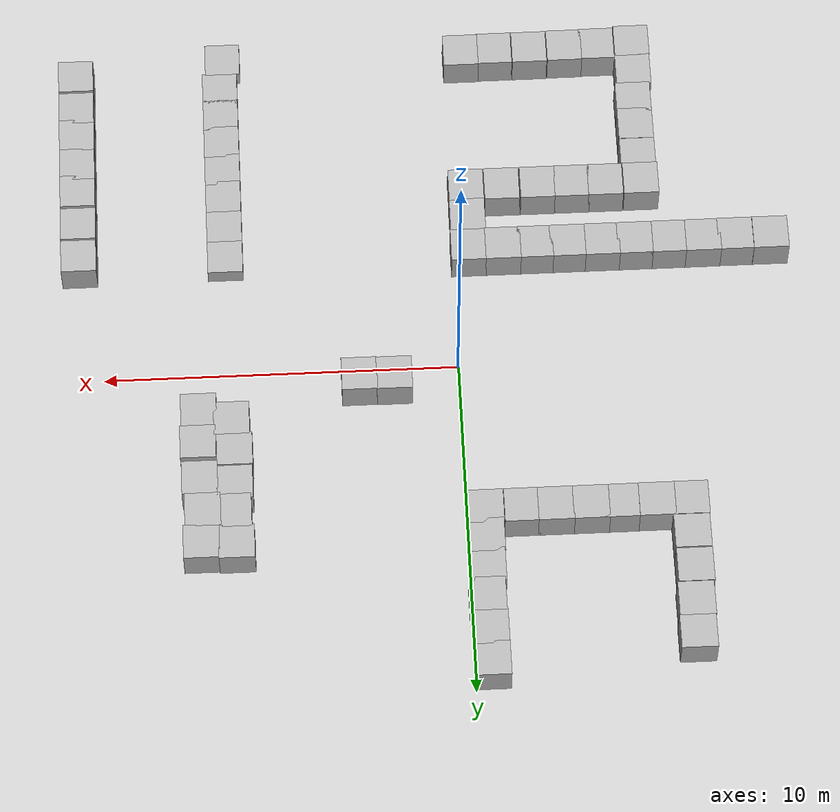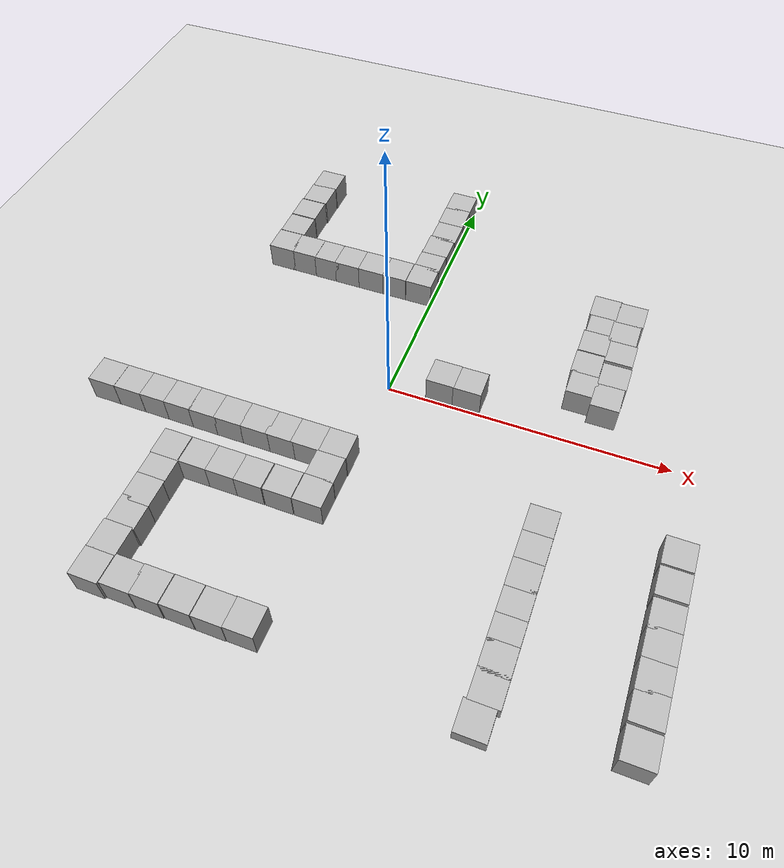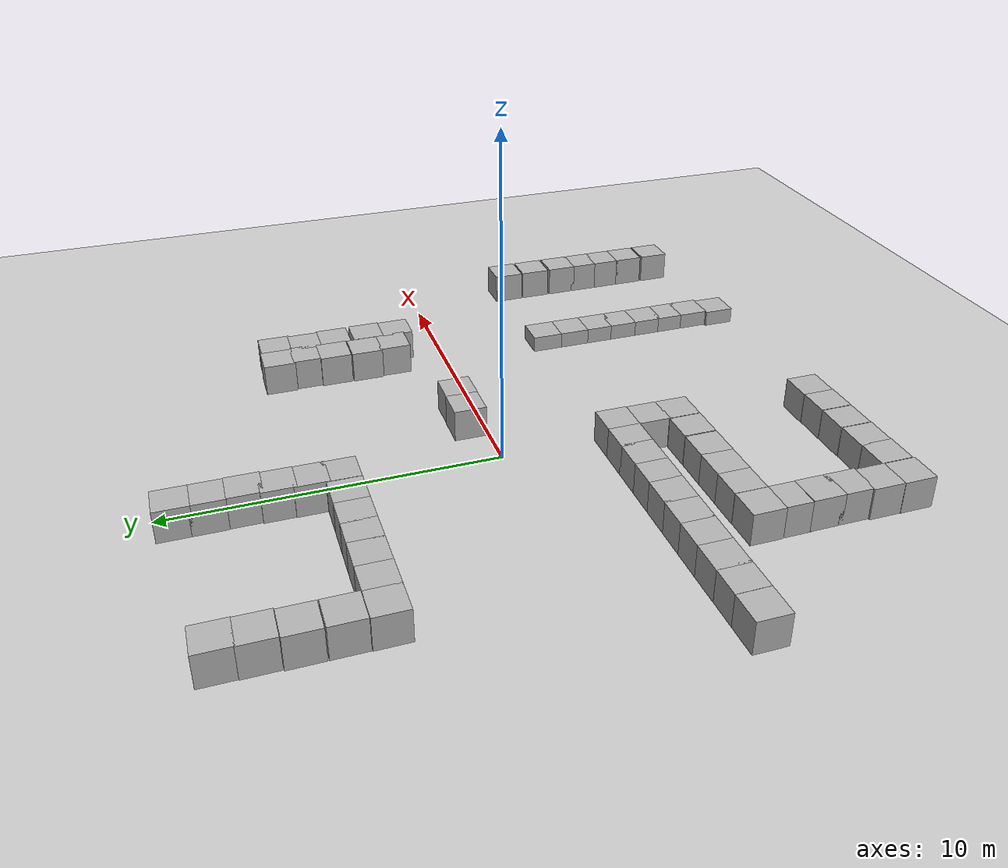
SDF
<sdf version='1.10'>
  <world name='empty'>
    <physics name='1ms' type='ignored'>
      <max_step_size>0.001</max_step_size>
      <real_time_factor>1</real_time_factor>
      <real_time_update_rate>1000</real_time_update_rate>
    </physics>
    <plugin name='gz::sim::systems::Physics' filename='gz-sim-physics-system'/>
    <plugin name='gz::sim::systems::UserCommands' filename='gz-sim-user-commands-system'/>
    <plugin name='gz::sim::systems::SceneBroadcaster' filename='gz-sim-scene-broadcaster-system'/>
    <plugin name='gz::sim::systems::Contact' filename='gz-sim-contact-system'/>
    <gravity>0 0 -9.8000000000000007</gravity>
    <magnetic_field>5.5644999999999998e-06 2.2875799999999999e-05 -4.2388400000000002e-05</magnetic_field>
    <atmosphere type='adiabatic'/>
    <scene>
      <ambient>0.400000006 0.400000006 0.400000006 1</ambient>
      <background>0.699999988 0.699999988 0.699999988 1</background>
      <shadows>true</shadows>
    </scene>
    <model name='ground_plane'>
      <static>true</static>
      <link name='link'>
        <collision name='collision'>
          <geometry>
            <plane>
              <normal>0 0 1</normal>
              <size>100 100</size>
            </plane>
          </geometry>
          <surface>
            <friction>
              <ode/>
            </friction>
            <bounce/>
            <contact/>
          </surface>
        </collision>
        <visual name='visual'>
          <geometry>
            <plane>
              <normal>0 0 1</normal>
              <size>100 100</size>
            </plane>
          </geometry>
          <material>
            <ambient>0.800000012 0.800000012 0.800000012 1</ambient>
            <diffuse>0.800000012 0.800000012 0.800000012 1</diffuse>
            <specular>0.800000012 0.800000012 0.800000012 1</specular>
          </material>
        </visual>
        <pose>0 0 0 0 0 0</pose>
        <inertial>
          <pose>0 0 0 0 0 0</pose>
          <mass>1</mass>
          <inertia>
            <ixx>1</ixx>
            <ixy>0</ixy>
            <ixz>0</ixz>
            <iyy>1</iyy>
            <iyz>0</iyz>
            <izz>1</izz>
          </inertia>
        </inertial>
        <enable_wind>false</enable_wind>
      </link>
      <pose>0 0 0 0 0 0</pose>
      <self_collide>false</self_collide>
    </model>
    <model name='box'>
      <pose>-0.45962236093902187 -3.4321811878695145 0.5 0 0 0</pose>
      <link name='box_link'>
        <inertial>
          <inertia>
            <ixx>0.16666</ixx>
            <ixy>0</ixy>
            <ixz>0</ixz>
            <iyy>0.16666</iyy>
            <iyz>0</iyz>
            <izz>0.16666</izz>
          </inertia>
          <mass>1</mass>
          <pose>0 0 0 0 0 0</pose>
        </inertial>
        <collision name='box_collision'>
          <geometry>
            <box>
              <size>1 1 1</size>
            </box>
          </geometry>
          <surface>
            <friction>
              <ode/>
            </friction>
            <bounce/>
            <contact/>
          </surface>
        </collision>
        <visual name='box_visual'>
          <geometry>
            <box>
              <size>1 1 1</size>
            </box>
          </geometry>
          <material>
            <ambient>0.300000012 0.300000012 0.300000012 1</ambient>
            <diffuse>0.699999988 0.699999988 0.699999988 1</diffuse>
            <specular>1 1 1 1</specular>
          </material>
        </visual>
        <pose>0 0 0 0 0 0</pose>
        <enable_wind>false</enable_wind>
      </link>
      <static>true</static>
      <self_collide>false</self_collide>
    </model>
    <model name='box_0'>
      <pose>-1.437559962272644 -3.4321799278259277 0.5 0 0 0</pose>
      <link name='box_link'>
        <inertial>
          <inertia>
            <ixx>0.16666</ixx>
            <ixy>0</ixy>
            <ixz>0</ixz>
            <iyy>0.16666</iyy>
            <iyz>0</iyz>
            <izz>0.16666</izz>
          </inertia>
          <mass>1</mass>
          <pose>0 0 0 0 0 0</pose>
        </inertial>
        <collision name='box_collision'>
          <geometry>
            <box>
              <size>1 1 1</size>
            </box>
          </geometry>
          <surface>
            <friction>
              <ode/>
            </friction>
            <bounce/>
            <contact/>
          </surface>
        </collision>
        <visual name='box_visual'>
          <geometry>
            <box>
              <size>1 1 1</size>
            </box>
          </geometry>
          <material>
            <ambient>0.300000012 0.300000012 0.300000012 1</ambient>
            <diffuse>0.699999988 0.699999988 0.699999988 1</diffuse>
            <specular>1 1 1 1</specular>
          </material>
        </visual>
        <pose>0 0 0 0 0 0</pose>
        <enable_wind>false</enable_wind>
      </link>
      <static>true</static>
      <self_collide>false</self_collide>
    </model>
    <model name='box_1'>
      <pose>-2.3603498935699463 -3.4321799278259277 0.5 0 0 0</pose>
      <link name='box_link'>
        <inertial>
          <inertia>
            <ixx>0.16666</ixx>
            <ixy>0</ixy>
            <ixz>0</ixz>
            <iyy>0.16666</iyy>
            <iyz>0</iyz>
            <izz>0.16666</izz>
          </inertia>
          <mass>1</mass>
          <pose>0 0 0 0 0 0</pose>
        </inertial>
        <collision name='box_collision'>
          <geometry>
            <box>
              <size>1 1 1</size>
            </box>
          </geometry>
          <surface>
            <friction>
              <ode/>
            </friction>
            <bounce/>
            <contact/>
          </surface>
        </collision>
        <visual name='box_visual'>
          <geometry>
            <box>
              <size>1 1 1</size>
            </box>
          </geometry>
          <material>
            <ambient>0.300000012 0.300000012 0.300000012 1</ambient>
            <diffuse>0.699999988 0.699999988 0.699999988 1</diffuse>
            <specular>1 1 1 1</specular>
          </material>
        </visual>
        <pose>0 0 0 0 0 0</pose>
        <enable_wind>false</enable_wind>
      </link>
      <static>true</static>
      <self_collide>false</self_collide>
    </model>
    <model name='box_2'>
      <pose>-3.2832300662994385 -3.4321799278259277 0.5 0 0 0</pose>
      <link name='box_link'>
        <inertial>
          <inertia>
            <ixx>0.16666</ixx>
            <ixy>0</ixy>
            <ixz>0</ixz>
            <iyy>0.16666</iyy>
            <iyz>0</iyz>
            <izz>0.16666</izz>
          </inertia>
          <mass>1</mass>
          <pose>0 0 0 0 0 0</pose>
        </inertial>
        <collision name='box_collision'>
          <geometry>
            <box>
              <size>1 1 1</size>
            </box>
          </geometry>
          <surface>
            <friction>
              <ode/>
            </friction>
            <bounce/>
            <contact/>
          </surface>
        </collision>
        <visual name='box_visual'>
          <geometry>
            <box>
              <size>1 1 1</size>
            </box>
          </geometry>
          <material>
            <ambient>0.300000012 0.300000012 0.300000012 1</ambient>
            <diffuse>0.699999988 0.699999988 0.699999988 1</diffuse>
            <specular>1 1 1 1</specular>
          </material>
        </visual>
        <pose>0 0 0 0 0 0</pose>
        <enable_wind>false</enable_wind>
      </link>
      <static>true</static>
      <self_collide>false</self_collide>
    </model>
    <model name='box_3'>
      <pose>-4.2610697746276855 -3.4321799278259277 0.5 0 0 0</pose>
      <link name='box_link'>
        <inertial>
          <inertia>
            <ixx>0.16666</ixx>
            <ixy>0</ixy>
            <ixz>0</ixz>
            <iyy>0.16666</iyy>
            <iyz>0</iyz>
            <izz>0.16666</izz>
          </inertia>
          <mass>1</mass>
          <pose>0 0 0 0 0 0</pose>
        </inertial>
        <collision name='box_collision'>
          <geometry>
            <box>
              <size>1 1 1</size>
            </box>
          </geometry>
          <surface>
            <friction>
              <ode/>
            </friction>
            <bounce/>
            <contact/>
          </surface>
        </collision>
        <visual name='box_visual'>
          <geometry>
            <box>
              <size>1 1 1</size>
            </box>
          </geometry>
          <material>
            <ambient>0.300000012 0.300000012 0.300000012 1</ambient>
            <diffuse>0.699999988 0.699999988 0.699999988 1</diffuse>
            <specular>1 1 1 1</specular>
          </material>
        </visual>
        <pose>0 0 0 0 0 0</pose>
        <enable_wind>false</enable_wind>
      </link>
      <static>true</static>
      <self_collide>false</self_collide>
    </model>
    <model name='box_4'>
      <pose>-5.1977601051330566 -3.4321799278259277 0.5 0 0 0</pose>
      <link name='box_link'>
        <inertial>
          <inertia>
            <ixx>0.16666</ixx>
            <ixy>0</ixy>
            <ixz>0</ixz>
            <iyy>0.16666</iyy>
            <iyz>0</iyz>
            <izz>0.16666</izz>
          </inertia>
          <mass>1</mass>
          <pose>0 0 0 0 0 0</pose>
        </inertial>
        <collision name='box_collision'>
          <geometry>
            <box>
              <size>1 1 1</size>
            </box>
          </geometry>
          <surface>
            <friction>
              <ode/>
            </friction>
            <bounce/>
            <contact/>
          </surface>
        </collision>
        <visual name='box_visual'>
          <geometry>
            <box>
              <size>1 1 1</size>
            </box>
          </geometry>
          <material>
            <ambient>0.300000012 0.300000012 0.300000012 1</ambient>
            <diffuse>0.699999988 0.699999988 0.699999988 1</diffuse>
            <specular>1 1 1 1</specular>
          </material>
        </visual>
        <pose>0 0 0 0 0 0</pose>
        <enable_wind>false</enable_wind>
      </link>
      <static>true</static>
      <self_collide>false</self_collide>
    </model>
    <model name='box_5'>
      <pose>-6.1482501029968262 -3.4321799278259277 0.5 0 0 0</pose>
      <link name='box_link'>
        <inertial>
          <inertia>
            <ixx>0.16666</ixx>
            <ixy>0</ixy>
            <ixz>0</ixz>
            <iyy>0.16666</iyy>
            <iyz>0</iyz>
            <izz>0.16666</izz>
          </inertia>
          <mass>1</mass>
          <pose>0 0 0 0 0 0</pose>
        </inertial>
        <collision name='box_collision'>
          <geometry>
            <box>
              <size>1 1 1</size>
            </box>
          </geometry>
          <surface>
            <friction>
              <ode/>
            </friction>
            <bounce/>
            <contact/>
          </surface>
        </collision>
        <visual name='box_visual'>
          <geometry>
            <box>
              <size>1 1 1</size>
            </box>
          </geometry>
          <material>
            <ambient>0.300000012 0.300000012 0.300000012 1</ambient>
            <diffuse>0.699999988 0.699999988 0.699999988 1</diffuse>
            <specular>1 1 1 1</specular>
          </material>
        </visual>
        <pose>0 0 0 0 0 0</pose>
        <enable_wind>false</enable_wind>
      </link>
      <static>true</static>
      <self_collide>false</self_collide>
    </model>
    <model name='box_6'>
      <pose>-7.1462202072143555 -3.4321799278259277 0.5 0 0 0</pose>
      <link name='box_link'>
        <inertial>
          <inertia>
            <ixx>0.16666</ixx>
            <ixy>0</ixy>
            <ixz>0</ixz>
            <iyy>0.16666</iyy>
            <iyz>0</iyz>
            <izz>0.16666</izz>
          </inertia>
          <mass>1</mass>
          <pose>0 0 0 0 0 0</pose>
        </inertial>
        <collision name='box_collision'>
          <geometry>
            <box>
              <size>1 1 1</size>
            </box>
          </geometry>
          <surface>
            <friction>
              <ode/>
            </friction>
            <bounce/>
            <contact/>
          </surface>
        </collision>
        <visual name='box_visual'>
          <geometry>
            <box>
              <size>1 1 1</size>
            </box>
          </geometry>
          <material>
            <ambient>0.300000012 0.300000012 0.300000012 1</ambient>
            <diffuse>0.699999988 0.699999988 0.699999988 1</diffuse>
            <specular>1 1 1 1</specular>
          </material>
        </visual>
        <pose>0 0 0 0 0 0</pose>
        <enable_wind>false</enable_wind>
      </link>
      <static>true</static>
      <self_collide>false</self_collide>
    </model>
    <model name='box_7'>
      <pose>-8.0709496915400525 -3.4372660996707891 0.5 0 0 0</pose>
      <link name='box_link'>
        <inertial>
          <inertia>
            <ixx>0.16666</ixx>
            <ixy>0</ixy>
            <ixz>0</ixz>
            <iyy>0.16666</iyy>
            <iyz>0</iyz>
            <izz>0.16666</izz>
          </inertia>
          <mass>1</mass>
          <pose>0 0 0 0 0 0</pose>
        </inertial>
        <collision name='box_collision'>
          <geometry>
            <box>
              <size>1 1 1</size>
            </box>
          </geometry>
          <surface>
            <friction>
              <ode/>
            </friction>
            <bounce/>
            <contact/>
          </surface>
        </collision>
        <visual name='box_visual'>
          <geometry>
            <box>
              <size>1 1 1</size>
            </box>
          </geometry>
          <material>
            <ambient>0.300000012 0.300000012 0.300000012 1</ambient>
            <diffuse>0.699999988 0.699999988 0.699999988 1</diffuse>
            <specular>1 1 1 1</specular>
          </material>
        </visual>
        <pose>0 0 0 0 0 0</pose>
        <enable_wind>false</enable_wind>
      </link>
      <static>true</static>
      <self_collide>false</self_collide>
    </model>
    <model name='box_8'>
      <pose>-9.0756287588108506 -3.4372660640371873 0.5 0 0 0</pose>
      <link name='box_link'>
        <inertial>
          <inertia>
            <ixx>0.16666</ixx>
            <ixy>0</ixy>
            <ixz>0</ixz>
            <iyy>0.16666</iyy>
            <iyz>0</iyz>
            <izz>0.16666</izz>
          </inertia>
          <mass>1</mass>
          <pose>0 0 0 0 0 0</pose>
        </inertial>
        <collision name='box_collision'>
          <geometry>
            <box>
              <size>1 1 1</size>
            </box>
          </geometry>
          <surface>
            <friction>
              <ode/>
            </friction>
            <bounce/>
            <contact/>
          </surface>
        </collision>
        <visual name='box_visual'>
          <geometry>
            <box>
              <size>1 1 1</size>
            </box>
          </geometry>
          <material>
            <ambient>0.300000012 0.300000012 0.300000012 1</ambient>
            <diffuse>0.699999988 0.699999988 0.699999988 1</diffuse>
            <specular>1 1 1 1</specular>
          </material>
        </visual>
        <pose>0 0 0 0 0 0</pose>
        <enable_wind>false</enable_wind>
      </link>
      <static>true</static>
      <self_collide>false</self_collide>
    </model>
    <model name='box_9'>
      <pose>-0.48098175029762213 -4.4153764900574703 0.5 0 0 0</pose>
      <link name='box_link'>
        <inertial>
          <inertia>
            <ixx>0.16666</ixx>
            <ixy>0</ixy>
            <ixz>0</ixz>
            <iyy>0.16666</iyy>
            <iyz>0</iyz>
            <izz>0.16666</izz>
          </inertia>
          <mass>1</mass>
          <pose>0 0 0 0 0 0</pose>
        </inertial>
        <collision name='box_collision'>
          <geometry>
            <box>
              <size>1 1 1</size>
            </box>
          </geometry>
          <surface>
            <friction>
              <ode/>
            </friction>
            <bounce/>
            <contact/>
          </surface>
        </collision>
        <visual name='box_visual'>
          <geometry>
            <box>
              <size>1 1 1</size>
            </box>
          </geometry>
          <material>
            <ambient>0.300000012 0.300000012 0.300000012 1</ambient>
            <diffuse>0.699999988 0.699999988 0.699999988 1</diffuse>
            <specular>1 1 1 1</specular>
          </material>
        </visual>
        <pose>0 0 0 0 0 0</pose>
        <enable_wind>false</enable_wind>
      </link>
      <static>true</static>
      <self_collide>false</self_collide>
    </model>
    <model name='box_10'>
      <pose>-0.48743896738457204 -5.377515620313809 0.5 0 0 0</pose>
      <link name='box_link'>
        <inertial>
          <inertia>
            <ixx>0.16666</ixx>
            <ixy>0</ixy>
            <ixz>0</ixz>
            <iyy>0.16666</iyy>
            <iyz>0</iyz>
            <izz>0.16666</izz>
          </inertia>
          <mass>1</mass>
          <pose>0 0 0 0 0 0</pose>
        </inertial>
        <collision name='box_collision'>
          <geometry>
            <box>
              <size>1 1 1</size>
            </box>
          </geometry>
          <surface>
            <friction>
              <ode/>
            </friction>
            <bounce/>
            <contact/>
          </surface>
        </collision>
        <visual name='box_visual'>
          <geometry>
            <box>
              <size>1 1 1</size>
            </box>
          </geometry>
          <material>
            <ambient>0.300000012 0.300000012 0.300000012 1</ambient>
            <diffuse>0.699999988 0.699999988 0.699999988 1</diffuse>
            <specular>1 1 1 1</specular>
          </material>
        </visual>
        <pose>0 0 0 0 0 0</pose>
        <enable_wind>false</enable_wind>
      </link>
      <static>true</static>
      <self_collide>false</self_collide>
    </model>
    <model name='box_13'>
      <pose>-1.5068099498748779 -5.3775200843811035 0.5 0 0 0</pose>
      <link name='box_link'>
        <inertial>
          <inertia>
            <ixx>0.16666</ixx>
            <ixy>0</ixy>
            <ixz>0</ixz>
            <iyy>0.16666</iyy>
            <iyz>0</iyz>
            <izz>0.16666</izz>
          </inertia>
          <mass>1</mass>
          <pose>0 0 0 0 0 0</pose>
        </inertial>
        <collision name='box_collision'>
          <geometry>
            <box>
              <size>1 1 1</size>
            </box>
          </geometry>
          <surface>
            <friction>
              <ode/>
            </friction>
            <bounce/>
            <contact/>
          </surface>
        </collision>
        <visual name='box_visual'>
          <geometry>
            <box>
              <size>1 1 1</size>
            </box>
          </geometry>
          <material>
            <ambient>0.300000012 0.300000012 0.300000012 1</ambient>
            <diffuse>0.699999988 0.699999988 0.699999988 1</diffuse>
            <specular>1 1 1 1</specular>
          </material>
        </visual>
        <pose>0 0 0 0 0 0</pose>
        <enable_wind>false</enable_wind>
      </link>
      <static>true</static>
      <self_collide>false</self_collide>
    </model>
    <model name='box_14'>
      <pose>-2.5399200916290283 -5.3775200843811035 0.5 0 0 0</pose>
      <link name='box_link'>
        <inertial>
          <inertia>
            <ixx>0.16666</ixx>
            <ixy>0</ixy>
            <ixz>0</ixz>
            <iyy>0.16666</iyy>
            <iyz>0</iyz>
            <izz>0.16666</izz>
          </inertia>
          <mass>1</mass>
          <pose>0 0 0 0 0 0</pose>
        </inertial>
        <collision name='box_collision'>
          <geometry>
            <box>
              <size>1 1 1</size>
            </box>
          </geometry>
          <surface>
            <friction>
              <ode/>
            </friction>
            <bounce/>
            <contact/>
          </surface>
        </collision>
        <visual name='box_visual'>
          <geometry>
            <box>
              <size>1 1 1</size>
            </box>
          </geometry>
          <material>
            <ambient>0.300000012 0.300000012 0.300000012 1</ambient>
            <diffuse>0.699999988 0.699999988 0.699999988 1</diffuse>
            <specular>1 1 1 1</specular>
          </material>
        </visual>
        <pose>0 0 0 0 0 0</pose>
        <enable_wind>false</enable_wind>
      </link>
      <static>true</static>
      <self_collide>false</self_collide>
    </model>
    <model name='box_15'>
      <pose>-3.5179600715637207 -5.3775200843811035 0.5 0 0 0</pose>
      <link name='box_link'>
        <inertial>
          <inertia>
            <ixx>0.16666</ixx>
            <ixy>0</ixy>
            <ixz>0</ixz>
            <iyy>0.16666</iyy>
            <iyz>0</iyz>
            <izz>0.16666</izz>
          </inertia>
          <mass>1</mass>
          <pose>0 0 0 0 0 0</pose>
        </inertial>
        <collision name='box_collision'>
          <geometry>
            <box>
              <size>1 1 1</size>
            </box>
          </geometry>
          <surface>
            <friction>
              <ode/>
            </friction>
            <bounce/>
            <contact/>
          </surface>
        </collision>
        <visual name='box_visual'>
          <geometry>
            <box>
              <size>1 1 1</size>
            </box>
          </geometry>
          <material>
            <ambient>0.300000012 0.300000012 0.300000012 1</ambient>
            <diffuse>0.699999988 0.699999988 0.699999988 1</diffuse>
            <specular>1 1 1 1</specular>
          </material>
        </visual>
        <pose>0 0 0 0 0 0</pose>
        <enable_wind>false</enable_wind>
      </link>
      <static>true</static>
      <self_collide>false</self_collide>
    </model>
    <model name='box_11'>
      <pose>-4.4819397926330566 -5.3775200843811035 0.5 0 0 0</pose>
      <link name='box_link'>
        <inertial>
          <inertia>
            <ixx>0.16666</ixx>
            <ixy>0</ixy>
            <ixz>0</ixz>
            <iyy>0.16666</iyy>
            <iyz>0</iyz>
            <izz>0.16666</izz>
          </inertia>
          <mass>1</mass>
          <pose>0 0 0 0 0 0</pose>
        </inertial>
        <collision name='box_collision'>
          <geometry>
            <box>
              <size>1 1 1</size>
            </box>
          </geometry>
          <surface>
            <friction>
              <ode/>
            </friction>
            <bounce/>
            <contact/>
          </surface>
        </collision>
        <visual name='box_visual'>
          <geometry>
            <box>
              <size>1 1 1</size>
            </box>
          </geometry>
          <material>
            <ambient>0.300000012 0.300000012 0.300000012 1</ambient>
            <diffuse>0.699999988 0.699999988 0.699999988 1</diffuse>
            <specular>1 1 1 1</specular>
          </material>
        </visual>
        <pose>0 0 0 0 0 0</pose>
        <enable_wind>false</enable_wind>
      </link>
      <static>true</static>
      <self_collide>false</self_collide>
    </model>
    <model name='box_16'>
      <pose>-5.5012998580932617 -5.3775200843811035 0.51010000705718994 0 0 0</pose>
      <link name='box_link'>
        <inertial>
          <inertia>
            <ixx>0.16666</ixx>
            <ixy>0</ixy>
            <ixz>0</ixz>
            <iyy>0.16666</iyy>
            <iyz>0</iyz>
            <izz>0.16666</izz>
          </inertia>
          <mass>1</mass>
          <pose>0 0 0 0 0 0</pose>
        </inertial>
        <collision name='box_collision'>
          <geometry>
            <box>
              <size>1 1 1</size>
            </box>
          </geometry>
          <surface>
            <friction>
              <ode/>
            </friction>
            <bounce/>
            <contact/>
          </surface>
        </collision>
        <visual name='box_visual'>
          <geometry>
            <box>
              <size>1 1 1</size>
            </box>
          </geometry>
          <material>
            <ambient>0.300000012 0.300000012 0.300000012 1</ambient>
            <diffuse>0.699999988 0.699999988 0.699999988 1</diffuse>
            <specular>1 1 1 1</specular>
          </material>
        </visual>
        <pose>0 0 0 0 0 0</pose>
        <enable_wind>false</enable_wind>
      </link>
      <static>true</static>
      <self_collide>false</self_collide>
    </model>
    <model name='box_17'>
      <pose>-5.4737473399962955 -6.3141155514986824 0.5 0 0 0</pose>
      <link name='box_link'>
        <inertial>
          <inertia>
            <ixx>0.16666</ixx>
            <ixy>0</ixy>
            <ixz>0</ixz>
            <iyy>0.16666</iyy>
            <iyz>0</iyz>
            <izz>0.16666</izz>
          </inertia>
          <mass>1</mass>
          <pose>0 0 0 0 0 0</pose>
        </inertial>
        <collision name='box_collision'>
          <geometry>
            <box>
              <size>1 1 1</size>
            </box>
          </geometry>
          <surface>
            <friction>
              <ode/>
            </friction>
            <bounce/>
            <contact/>
          </surface>
        </collision>
        <visual name='box_visual'>
          <geometry>
            <box>
              <size>1 1 1</size>
            </box>
          </geometry>
          <material>
            <ambient>0.300000012 0.300000012 0.300000012 1</ambient>
            <diffuse>0.699999988 0.699999988 0.699999988 1</diffuse>
            <specular>1 1 1 1</specular>
          </material>
        </visual>
        <pose>0 0 0 0 0 0</pose>
        <enable_wind>false</enable_wind>
      </link>
      <static>true</static>
      <self_collide>false</self_collide>
    </model>
    <model name='box_18'>
      <pose>-5.473750114440918 -7.1958298683166504 0.51010000705718994 0 0 0</pose>
      <link name='box_link'>
        <inertial>
          <inertia>
            <ixx>0.16666</ixx>
            <ixy>0</ixy>
            <ixz>0</ixz>
            <iyy>0.16666</iyy>
            <iyz>0</iyz>
            <izz>0.16666</izz>
          </inertia>
          <mass>1</mass>
          <pose>0 0 0 0 0 0</pose>
        </inertial>
        <collision name='box_collision'>
          <geometry>
            <box>
              <size>1 1 1</size>
            </box>
          </geometry>
          <surface>
            <friction>
              <ode/>
            </friction>
            <bounce/>
            <contact/>
          </surface>
        </collision>
        <visual name='box_visual'>
          <geometry>
            <box>
              <size>1 1 1</size>
            </box>
          </geometry>
          <material>
            <ambient>0.300000012 0.300000012 0.300000012 1</ambient>
            <diffuse>0.699999988 0.699999988 0.699999988 1</diffuse>
            <specular>1 1 1 1</specular>
          </material>
        </visual>
        <pose>0 0 0 0 0 0</pose>
        <enable_wind>false</enable_wind>
      </link>
      <static>true</static>
      <self_collide>false</self_collide>
    </model>
    <model name='box_19'>
      <pose>-5.473750114440918 -8.0638999938964844 0.51010000705718994 0 0 0</pose>
      <link name='box_link'>
        <inertial>
          <inertia>
            <ixx>0.16666</ixx>
            <ixy>0</ixy>
            <ixz>0</ixz>
            <iyy>0.16666</iyy>
            <iyz>0</iyz>
            <izz>0.16666</izz>
          </inertia>
          <mass>1</mass>
          <pose>0 0 0 0 0 0</pose>
        </inertial>
        <collision name='box_collision'>
          <geometry>
            <box>
              <size>1 1 1</size>
            </box>
          </geometry>
          <surface>
            <friction>
              <ode/>
            </friction>
            <bounce/>
            <contact/>
          </surface>
        </collision>
        <visual name='box_visual'>
          <geometry>
            <box>
              <size>1 1 1</size>
            </box>
          </geometry>
          <material>
            <ambient>0.300000012 0.300000012 0.300000012 1</ambient>
            <diffuse>0.699999988 0.699999988 0.699999988 1</diffuse>
            <specular>1 1 1 1</specular>
          </material>
        </visual>
        <pose>0 0 0 0 0 0</pose>
        <enable_wind>false</enable_wind>
      </link>
      <static>true</static>
      <self_collide>false</self_collide>
    </model>
    <model name='box_20'>
      <pose>-5.5288400650024414 -9.0141401290893555 0.51010000705718994 0 0 0</pose>
      <link name='box_link'>
        <inertial>
          <inertia>
            <ixx>0.16666</ixx>
            <ixy>0</ixy>
            <ixz>0</ixz>
            <iyy>0.16666</iyy>
            <iyz>0</iyz>
            <izz>0.16666</izz>
          </inertia>
          <mass>1</mass>
          <pose>0 0 0 0 0 0</pose>
        </inertial>
        <collision name='box_collision'>
          <geometry>
            <box>
              <size>1 1 1</size>
            </box>
          </geometry>
          <surface>
            <friction>
              <ode/>
            </friction>
            <bounce/>
            <contact/>
          </surface>
        </collision>
        <visual name='box_visual'>
          <geometry>
            <box>
              <size>1 1 1</size>
            </box>
          </geometry>
          <material>
            <ambient>0.300000012 0.300000012 0.300000012 1</ambient>
            <diffuse>0.699999988 0.699999988 0.699999988 1</diffuse>
            <specular>1 1 1 1</specular>
          </material>
        </visual>
        <pose>0 0 0 0 0 0</pose>
        <enable_wind>false</enable_wind>
      </link>
      <static>true</static>
      <self_collide>false</self_collide>
    </model>
    <model name='box_21'>
      <pose>-5.5426301956176758 -9.992340087890625 0.51010000705718994 0 0 0</pose>
      <link name='box_link'>
        <inertial>
          <inertia>
            <ixx>0.16666</ixx>
            <ixy>0</ixy>
            <ixz>0</ixz>
            <iyy>0.16666</iyy>
            <iyz>0</iyz>
            <izz>0.16666</izz>
          </inertia>
          <mass>1</mass>
          <pose>0 0 0 0 0 0</pose>
        </inertial>
        <collision name='box_collision'>
          <geometry>
            <box>
              <size>1 1 1</size>
            </box>
          </geometry>
          <surface>
            <friction>
              <ode/>
            </friction>
            <bounce/>
            <contact/>
          </surface>
        </collision>
        <visual name='box_visual'>
          <geometry>
            <box>
              <size>1 1 1</size>
            </box>
          </geometry>
          <material>
            <ambient>0.300000012 0.300000012 0.300000012 1</ambient>
            <diffuse>0.699999988 0.699999988 0.699999988 1</diffuse>
            <specular>1 1 1 1</specular>
          </material>
        </visual>
        <pose>0 0 0 0 0 0</pose>
        <enable_wind>false</enable_wind>
      </link>
      <static>true</static>
      <self_collide>false</self_collide>
    </model>
    <model name='box_12'>
      <pose>-4.5232601165771484 -9.9371004104614258 0.51010000705718994 0 0 0</pose>
      <link name='box_link'>
        <inertial>
          <inertia>
            <ixx>0.16666</ixx>
            <ixy>0</ixy>
            <ixz>0</ixz>
            <iyy>0.16666</iyy>
            <iyz>0</iyz>
            <izz>0.16666</izz>
          </inertia>
          <mass>1</mass>
          <pose>0 0 0 0 0 0</pose>
        </inertial>
        <collision name='box_collision'>
          <geometry>
            <box>
              <size>1 1 1</size>
            </box>
          </geometry>
          <surface>
            <friction>
              <ode/>
            </friction>
            <bounce/>
            <contact/>
          </surface>
        </collision>
        <visual name='box_visual'>
          <geometry>
            <box>
              <size>1 1 1</size>
            </box>
          </geometry>
          <material>
            <ambient>0.300000012 0.300000012 0.300000012 1</ambient>
            <diffuse>0.699999988 0.699999988 0.699999988 1</diffuse>
            <specular>1 1 1 1</specular>
          </material>
        </visual>
        <pose>0 0 0 0 0 0</pose>
        <enable_wind>false</enable_wind>
      </link>
      <static>true</static>
      <self_collide>false</self_collide>
    </model>
    <model name='box_22'>
      <pose>-3.5727999210357666 -9.9234695434570312 0.51010000705718994 0 0 0</pose>
      <link name='box_link'>
        <inertial>
          <inertia>
            <ixx>0.16666</ixx>
            <ixy>0</ixy>
            <ixz>0</ixz>
            <iyy>0.16666</iyy>
            <iyz>0</iyz>
            <izz>0.16666</izz>
          </inertia>
          <mass>1</mass>
          <pose>0 0 0 0 0 0</pose>
        </inertial>
        <collision name='box_collision'>
          <geometry>
            <box>
              <size>1 1 1</size>
            </box>
          </geometry>
          <surface>
            <friction>
              <ode/>
            </friction>
            <bounce/>
            <contact/>
          </surface>
        </collision>
        <visual name='box_visual'>
          <geometry>
            <box>
              <size>1 1 1</size>
            </box>
          </geometry>
          <material>
            <ambient>0.300000012 0.300000012 0.300000012 1</ambient>
            <diffuse>0.699999988 0.699999988 0.699999988 1</diffuse>
            <specular>1 1 1 1</specular>
          </material>
        </visual>
        <pose>0 0 0 0 0 0</pose>
        <enable_wind>false</enable_wind>
      </link>
      <static>true</static>
      <self_collide>false</self_collide>
    </model>
    <model name='box_23'>
      <pose>-2.5534501075744629 -9.9101800918579102 0.51010000705718994 0 0 0</pose>
      <link name='box_link'>
        <inertial>
          <inertia>
            <ixx>0.16666</ixx>
            <ixy>0</ixy>
            <ixz>0</ixz>
            <iyy>0.16666</iyy>
            <iyz>0</iyz>
            <izz>0.16666</izz>
          </inertia>
          <mass>1</mass>
          <pose>0 0 0 0 0 0</pose>
        </inertial>
        <collision name='box_collision'>
          <geometry>
            <box>
              <size>1 1 1</size>
            </box>
          </geometry>
          <surface>
            <friction>
              <ode/>
            </friction>
            <bounce/>
            <contact/>
          </surface>
        </collision>
        <visual name='box_visual'>
          <geometry>
            <box>
              <size>1 1 1</size>
            </box>
          </geometry>
          <material>
            <ambient>0.300000012 0.300000012 0.300000012 1</ambient>
            <diffuse>0.699999988 0.699999988 0.699999988 1</diffuse>
            <specular>1 1 1 1</specular>
          </material>
        </visual>
        <pose>0 0 0 0 0 0</pose>
        <enable_wind>false</enable_wind>
      </link>
      <static>true</static>
      <self_collide>false</self_collide>
    </model>
    <model name='box_24'>
      <pose>-1.5340800285339355 -9.9101800918579102 0.51010000705718994 0 0 0</pose>
      <link name='box_link'>
        <inertial>
          <inertia>
            <ixx>0.16666</ixx>
            <ixy>0</ixy>
            <ixz>0</ixz>
            <iyy>0.16666</iyy>
            <iyz>0</iyz>
            <izz>0.16666</izz>
          </inertia>
          <mass>1</mass>
          <pose>0 0 0 0 0 0</pose>
        </inertial>
        <collision name='box_collision'>
          <geometry>
            <box>
              <size>1 1 1</size>
            </box>
          </geometry>
          <surface>
            <friction>
              <ode/>
            </friction>
            <bounce/>
            <contact/>
          </surface>
        </collision>
        <visual name='box_visual'>
          <geometry>
            <box>
              <size>1 1 1</size>
            </box>
          </geometry>
          <material>
            <ambient>0.300000012 0.300000012 0.300000012 1</ambient>
            <diffuse>0.699999988 0.699999988 0.699999988 1</diffuse>
            <specular>1 1 1 1</specular>
          </material>
        </visual>
        <pose>0 0 0 0 0 0</pose>
        <enable_wind>false</enable_wind>
      </link>
      <static>true</static>
      <self_collide>false</self_collide>
    </model>
    <model name='box_25'>
      <pose>-0.5560610294342041 -9.8955001831054688 0.51010000705718994 0 0 0</pose>
      <link name='box_link'>
        <inertial>
          <inertia>
            <ixx>0.16666</ixx>
            <ixy>0</ixy>
            <ixz>0</ixz>
            <iyy>0.16666</iyy>
            <iyz>0</iyz>
            <izz>0.16666</izz>
          </inertia>
          <mass>1</mass>
          <pose>0 0 0 0 0 0</pose>
        </inertial>
        <collision name='box_collision'>
          <geometry>
            <box>
              <size>1 1 1</size>
            </box>
          </geometry>
          <surface>
            <friction>
              <ode/>
            </friction>
            <bounce/>
            <contact/>
          </surface>
        </collision>
        <visual name='box_visual'>
          <geometry>
            <box>
              <size>1 1 1</size>
            </box>
          </geometry>
          <material>
            <ambient>0.300000012 0.300000012 0.300000012 1</ambient>
            <diffuse>0.699999988 0.699999988 0.699999988 1</diffuse>
            <specular>1 1 1 1</specular>
          </material>
        </visual>
        <pose>0 0 0 0 0 0</pose>
        <enable_wind>false</enable_wind>
      </link>
      <static>true</static>
      <self_collide>false</self_collide>
    </model>
    <model name='box_26'>
      <pose>-0.44753930680156817 9.4330309621648745 0.5 0 0 0</pose>
      <link name='box_link'>
        <inertial>
          <inertia>
            <ixx>0.16666</ixx>
            <ixy>0</ixy>
            <ixz>0</ixz>
            <iyy>0.16666</iyy>
            <iyz>0</iyz>
            <izz>0.16666</izz>
          </inertia>
          <mass>1</mass>
          <pose>0 0 0 0 0 0</pose>
        </inertial>
        <collision name='box_collision'>
          <geometry>
            <box>
              <size>1 1 1</size>
            </box>
          </geometry>
          <surface>
            <friction>
              <ode/>
            </friction>
            <bounce/>
            <contact/>
          </surface>
        </collision>
        <visual name='box_visual'>
          <geometry>
            <box>
              <size>1 1 1</size>
            </box>
          </geometry>
          <material>
            <ambient>0.300000012 0.300000012 0.300000012 1</ambient>
            <diffuse>0.699999988 0.699999988 0.699999988 1</diffuse>
            <specular>1 1 1 1</specular>
          </material>
        </visual>
        <pose>0 0 0 0 0 0</pose>
        <enable_wind>false</enable_wind>
      </link>
      <static>true</static>
      <self_collide>false</self_collide>
    </model>
    <model name='box_27'>
      <pose>-0.44753930264989128 8.5017166457179663 0.5 0 0 0</pose>
      <link name='box_link'>
        <inertial>
          <inertia>
            <ixx>0.16666</ixx>
            <ixy>0</ixy>
            <ixz>0</ixz>
            <iyy>0.16666</iyy>
            <iyz>0</iyz>
            <izz>0.16666</izz>
          </inertia>
          <mass>1</mass>
          <pose>0 0 0 0 0 0</pose>
        </inertial>
        <collision name='box_collision'>
          <geometry>
            <box>
              <size>1 1 1</size>
            </box>
          </geometry>
          <surface>
            <friction>
              <ode/>
            </friction>
            <bounce/>
            <contact/>
          </surface>
        </collision>
        <visual name='box_visual'>
          <geometry>
            <box>
              <size>1 1 1</size>
            </box>
          </geometry>
          <material>
            <ambient>0.300000012 0.300000012 0.300000012 1</ambient>
            <diffuse>0.699999988 0.699999988 0.699999988 1</diffuse>
            <specular>1 1 1 1</specular>
          </material>
        </visual>
        <pose>0 0 0 0 0 0</pose>
        <enable_wind>false</enable_wind>
      </link>
      <static>true</static>
      <self_collide>false</self_collide>
    </model>
    <model name='box_28'>
      <pose>-0.42771745107901904 7.5089888810876442 0.5 0 0 0</pose>
      <link name='box_link'>
        <inertial>
          <inertia>
            <ixx>0.16666</ixx>
            <ixy>0</ixy>
            <ixz>0</ixz>
            <iyy>0.16666</iyy>
            <iyz>0</iyz>
            <izz>0.16666</izz>
          </inertia>
          <mass>1</mass>
          <pose>0 0 0 0 0 0</pose>
        </inertial>
        <collision name='box_collision'>
          <geometry>
            <box>
              <size>1 1 1</size>
            </box>
          </geometry>
          <surface>
            <friction>
              <ode/>
            </friction>
            <bounce/>
            <contact/>
          </surface>
        </collision>
        <visual name='box_visual'>
          <geometry>
            <box>
              <size>1 1 1</size>
            </box>
          </geometry>
          <material>
            <ambient>0.300000012 0.300000012 0.300000012 1</ambient>
            <diffuse>0.699999988 0.699999988 0.699999988 1</diffuse>
            <specular>1 1 1 1</specular>
          </material>
        </visual>
        <pose>0 0 0 0 0 0</pose>
        <enable_wind>false</enable_wind>
      </link>
      <static>true</static>
      <self_collide>false</self_collide>
    </model>
    <model name='box_29'>
      <pose>-0.46742406053170782 6.6169409865384967 0.5 0 0 0</pose>
      <link name='box_link'>
        <inertial>
          <inertia>
            <ixx>0.16666</ixx>
            <ixy>0</ixy>
            <ixz>0</ixz>
            <iyy>0.16666</iyy>
            <iyz>0</iyz>
            <izz>0.16666</izz>
          </inertia>
          <mass>1</mass>
          <pose>0 0 0 0 0 0</pose>
        </inertial>
        <collision name='box_collision'>
          <geometry>
            <box>
              <size>1 1 1</size>
            </box>
          </geometry>
          <surface>
            <friction>
              <ode/>
            </friction>
            <bounce/>
            <contact/>
          </surface>
        </collision>
        <visual name='box_visual'>
          <geometry>
            <box>
              <size>1 1 1</size>
            </box>
          </geometry>
          <material>
            <ambient>0.300000012 0.300000012 0.300000012 1</ambient>
            <diffuse>0.699999988 0.699999988 0.699999988 1</diffuse>
            <specular>1 1 1 1</specular>
          </material>
        </visual>
        <pose>0 0 0 0 0 0</pose>
        <enable_wind>false</enable_wind>
      </link>
      <static>true</static>
      <self_collide>false</self_collide>
    </model>
    <model name='box_30'>
      <pose>-0.48724595930397385 5.7228831728455845 0.5 0 0 0</pose>
      <link name='box_link'>
        <inertial>
          <inertia>
            <ixx>0.16666</ixx>
            <ixy>0</ixy>
            <ixz>0</ixz>
            <iyy>0.16666</iyy>
            <iyz>0</iyz>
            <izz>0.16666</izz>
          </inertia>
          <mass>1</mass>
          <pose>0 0 0 0 0 0</pose>
        </inertial>
        <collision name='box_collision'>
          <geometry>
            <box>
              <size>1 1 1</size>
            </box>
          </geometry>
          <surface>
            <friction>
              <ode/>
            </friction>
            <bounce/>
            <contact/>
          </surface>
        </collision>
        <visual name='box_visual'>
          <geometry>
            <box>
              <size>1 1 1</size>
            </box>
          </geometry>
          <material>
            <ambient>0.300000012 0.300000012 0.300000012 1</ambient>
            <diffuse>0.699999988 0.699999988 0.699999988 1</diffuse>
            <specular>1 1 1 1</specular>
          </material>
        </visual>
        <pose>0 0 0 0 0 0</pose>
        <enable_wind>false</enable_wind>
      </link>
      <static>true</static>
      <self_collide>false</self_collide>
    </model>
    <model name='box_31'>
      <pose>-0.5070679783821106 4.8519802093505859 0.5 0 0 0</pose>
      <link name='box_link'>
        <inertial>
          <inertia>
            <ixx>0.16666</ixx>
            <ixy>0</ixy>
            <ixz>0</ixz>
            <iyy>0.16666</iyy>
            <iyz>0</iyz>
            <izz>0.16666</izz>
          </inertia>
          <mass>1</mass>
          <pose>0 0 0 0 0 0</pose>
        </inertial>
        <collision name='box_collision'>
          <geometry>
            <box>
              <size>1 1 1</size>
            </box>
          </geometry>
          <surface>
            <friction>
              <ode/>
            </friction>
            <bounce/>
            <contact/>
          </surface>
        </collision>
        <visual name='box_visual'>
          <geometry>
            <box>
              <size>1 1 1</size>
            </box>
          </geometry>
          <material>
            <ambient>0.300000012 0.300000012 0.300000012 1</ambient>
            <diffuse>0.699999988 0.699999988 0.699999988 1</diffuse>
            <specular>1 1 1 1</specular>
          </material>
        </visual>
        <pose>0 0 0 0 0 0</pose>
        <enable_wind>false</enable_wind>
      </link>
      <static>true</static>
      <self_collide>false</self_collide>
    </model>
    <model name='box_32'>
      <pose>-1.5186699628829956 4.8519802093505859 0.5 0 0 0</pose>
      <link name='box_link'>
        <inertial>
          <inertia>
            <ixx>0.16666</ixx>
            <ixy>0</ixy>
            <ixz>0</ixz>
            <iyy>0.16666</iyy>
            <iyz>0</iyz>
            <izz>0.16666</izz>
          </inertia>
          <mass>1</mass>
          <pose>0 0 0 0 0 0</pose>
        </inertial>
        <collision name='box_collision'>
          <geometry>
            <box>
              <size>1 1 1</size>
            </box>
          </geometry>
          <surface>
            <friction>
              <ode/>
            </friction>
            <bounce/>
            <contact/>
          </surface>
        </collision>
        <visual name='box_visual'>
          <geometry>
            <box>
              <size>1 1 1</size>
            </box>
          </geometry>
          <material>
            <ambient>0.300000012 0.300000012 0.300000012 1</ambient>
            <diffuse>0.699999988 0.699999988 0.699999988 1</diffuse>
            <specular>1 1 1 1</specular>
          </material>
        </visual>
        <pose>0 0 0 0 0 0</pose>
        <enable_wind>false</enable_wind>
      </link>
      <static>true</static>
      <self_collide>false</self_collide>
    </model>
    <model name='box_33'>
      <pose>-2.450930118560791 4.8519802093505859 0.5 0 0 0</pose>
      <link name='box_link'>
        <inertial>
          <inertia>
            <ixx>0.16666</ixx>
            <ixy>0</ixy>
            <ixz>0</ixz>
            <iyy>0.16666</iyy>
            <iyz>0</iyz>
            <izz>0.16666</izz>
          </inertia>
          <mass>1</mass>
          <pose>0 0 0 0 0 0</pose>
        </inertial>
        <collision name='box_collision'>
          <geometry>
            <box>
              <size>1 1 1</size>
            </box>
          </geometry>
          <surface>
            <friction>
              <ode/>
            </friction>
            <bounce/>
            <contact/>
          </surface>
        </collision>
        <visual name='box_visual'>
          <geometry>
            <box>
              <size>1 1 1</size>
            </box>
          </geometry>
          <material>
            <ambient>0.300000012 0.300000012 0.300000012 1</ambient>
            <diffuse>0.699999988 0.699999988 0.699999988 1</diffuse>
            <specular>1 1 1 1</specular>
          </material>
        </visual>
        <pose>0 0 0 0 0 0</pose>
        <enable_wind>false</enable_wind>
      </link>
      <static>true</static>
      <self_collide>false</self_collide>
    </model>
    <model name='box_34'>
      <pose>-3.4228301048278809 4.8519802093505859 0.5 0 0 0</pose>
      <link name='box_link'>
        <inertial>
          <inertia>
            <ixx>0.16666</ixx>
            <ixy>0</ixy>
            <ixz>0</ixz>
            <iyy>0.16666</iyy>
            <iyz>0</iyz>
            <izz>0.16666</izz>
          </inertia>
          <mass>1</mass>
          <pose>0 0 0 0 0 0</pose>
        </inertial>
        <collision name='box_collision'>
          <geometry>
            <box>
              <size>1 1 1</size>
            </box>
          </geometry>
          <surface>
            <friction>
              <ode/>
            </friction>
            <bounce/>
            <contact/>
          </surface>
        </collision>
        <visual name='box_visual'>
          <geometry>
            <box>
              <size>1 1 1</size>
            </box>
          </geometry>
          <material>
            <ambient>0.300000012 0.300000012 0.300000012 1</ambient>
            <diffuse>0.699999988 0.699999988 0.699999988 1</diffuse>
            <specular>1 1 1 1</specular>
          </material>
        </visual>
        <pose>0 0 0 0 0 0</pose>
        <enable_wind>false</enable_wind>
      </link>
      <static>true</static>
      <self_collide>false</self_collide>
    </model>
    <model name='box_35'>
      <pose>-4.2757401466369629 4.8519802093505859 0.5 0 0 0</pose>
      <link name='box_link'>
        <inertial>
          <inertia>
            <ixx>0.16666</ixx>
            <ixy>0</ixy>
            <ixz>0</ixz>
            <iyy>0.16666</iyy>
            <iyz>0</iyz>
            <izz>0.16666</izz>
          </inertia>
          <mass>1</mass>
          <pose>0 0 0 0 0 0</pose>
        </inertial>
        <collision name='box_collision'>
          <geometry>
            <box>
              <size>1 1 1</size>
            </box>
          </geometry>
          <surface>
            <friction>
              <ode/>
            </friction>
            <bounce/>
            <contact/>
          </surface>
        </collision>
        <visual name='box_visual'>
          <geometry>
            <box>
              <size>1 1 1</size>
            </box>
          </geometry>
          <material>
            <ambient>0.300000012 0.300000012 0.300000012 1</ambient>
            <diffuse>0.699999988 0.699999988 0.699999988 1</diffuse>
            <specular>1 1 1 1</specular>
          </material>
        </visual>
        <pose>0 0 0 0 0 0</pose>
        <enable_wind>false</enable_wind>
      </link>
      <static>true</static>
      <self_collide>false</self_collide>
    </model>
    <model name='box_36'>
      <pose>-5.2476401329040527 4.8519802093505859 0.51010000705718994 0 0 0</pose>
      <link name='box_link'>
        <inertial>
          <inertia>
            <ixx>0.16666</ixx>
            <ixy>0</ixy>
            <ixz>0</ixz>
            <iyy>0.16666</iyy>
            <iyz>0</iyz>
            <izz>0.16666</izz>
          </inertia>
          <mass>1</mass>
          <pose>0 0 0 0 0 0</pose>
        </inertial>
        <collision name='box_collision'>
          <geometry>
            <box>
              <size>1 1 1</size>
            </box>
          </geometry>
          <surface>
            <friction>
              <ode/>
            </friction>
            <bounce/>
            <contact/>
          </surface>
        </collision>
        <visual name='box_visual'>
          <geometry>
            <box>
              <size>1 1 1</size>
            </box>
          </geometry>
          <material>
            <ambient>0.300000012 0.300000012 0.300000012 1</ambient>
            <diffuse>0.699999988 0.699999988 0.699999988 1</diffuse>
            <specular>1 1 1 1</specular>
          </material>
        </visual>
        <pose>0 0 0 0 0 0</pose>
        <enable_wind>false</enable_wind>
      </link>
      <static>true</static>
      <self_collide>false</self_collide>
    </model>
    <model name='box_37'>
      <pose>-6.1798901557922363 4.8519802093505859 0.51010000705718994 0 0 0</pose>
      <link name='box_link'>
        <inertial>
          <inertia>
            <ixx>0.16666</ixx>
            <ixy>0</ixy>
            <ixz>0</ixz>
            <iyy>0.16666</iyy>
            <iyz>0</iyz>
            <izz>0.16666</izz>
          </inertia>
          <mass>1</mass>
          <pose>0 0 0 0 0 0</pose>
        </inertial>
        <collision name='box_collision'>
          <geometry>
            <box>
              <size>1 1 1</size>
            </box>
          </geometry>
          <surface>
            <friction>
              <ode/>
            </friction>
            <bounce/>
            <contact/>
          </surface>
        </collision>
        <visual name='box_visual'>
          <geometry>
            <box>
              <size>1 1 1</size>
            </box>
          </geometry>
          <material>
            <ambient>0.300000012 0.300000012 0.300000012 1</ambient>
            <diffuse>0.699999988 0.699999988 0.699999988 1</diffuse>
            <specular>1 1 1 1</specular>
          </material>
        </visual>
        <pose>0 0 0 0 0 0</pose>
        <enable_wind>false</enable_wind>
      </link>
      <static>true</static>
      <self_collide>false</self_collide>
    </model>
    <model name='box_38'>
      <pose>-6.1600699424743652 5.8628301620483398 0.51010000705718994 0 0 0</pose>
      <link name='box_link'>
        <inertial>
          <inertia>
            <ixx>0.16666</ixx>
            <ixy>0</ixy>
            <ixz>0</ixz>
            <iyy>0.16666</iyy>
            <iyz>0</iyz>
            <izz>0.16666</izz>
          </inertia>
          <mass>1</mass>
          <pose>0 0 0 0 0 0</pose>
        </inertial>
        <collision name='box_collision'>
          <geometry>
            <box>
              <size>1 1 1</size>
            </box>
          </geometry>
          <surface>
            <friction>
              <ode/>
            </friction>
            <bounce/>
            <contact/>
          </surface>
        </collision>
        <visual name='box_visual'>
          <geometry>
            <box>
              <size>1 1 1</size>
            </box>
          </geometry>
          <material>
            <ambient>0.300000012 0.300000012 0.300000012 1</ambient>
            <diffuse>0.699999988 0.699999988 0.699999988 1</diffuse>
            <specular>1 1 1 1</specular>
          </material>
        </visual>
        <pose>0 0 0 0 0 0</pose>
        <enable_wind>false</enable_wind>
      </link>
      <static>true</static>
      <self_collide>false</self_collide>
    </model>
    <model name='box_39'>
      <pose>-6.1600699424743652 6.8938198089599609 0.51010000705718994 0 0 0</pose>
      <link name='box_link'>
        <inertial>
          <inertia>
            <ixx>0.16666</ixx>
            <ixy>0</ixy>
            <ixz>0</ixz>
            <iyy>0.16666</iyy>
            <iyz>0</iyz>
            <izz>0.16666</izz>
          </inertia>
          <mass>1</mass>
          <pose>0 0 0 0 0 0</pose>
        </inertial>
        <collision name='box_collision'>
          <geometry>
            <box>
              <size>1 1 1</size>
            </box>
          </geometry>
          <surface>
            <friction>
              <ode/>
            </friction>
            <bounce/>
            <contact/>
          </surface>
        </collision>
        <visual name='box_visual'>
          <geometry>
            <box>
              <size>1 1 1</size>
            </box>
          </geometry>
          <material>
            <ambient>0.300000012 0.300000012 0.300000012 1</ambient>
            <diffuse>0.699999988 0.699999988 0.699999988 1</diffuse>
            <specular>1 1 1 1</specular>
          </material>
        </visual>
        <pose>0 0 0 0 0 0</pose>
        <enable_wind>false</enable_wind>
      </link>
      <static>true</static>
      <self_collide>false</self_collide>
    </model>
    <model name='box_40'>
      <pose>-6.1218199729919434 7.9072399139404297 0.51010000705718994 0 0 0</pose>
      <link name='box_link'>
        <inertial>
          <inertia>
            <ixx>0.16666</ixx>
            <ixy>0</ixy>
            <ixz>0</ixz>
            <iyy>0.16666</iyy>
            <iyz>0</iyz>
            <izz>0.16666</izz>
          </inertia>
          <mass>1</mass>
          <pose>0 0 0 0 0 0</pose>
        </inertial>
        <collision name='box_collision'>
          <geometry>
            <box>
              <size>1 1 1</size>
            </box>
          </geometry>
          <surface>
            <friction>
              <ode/>
            </friction>
            <bounce/>
            <contact/>
          </surface>
        </collision>
        <visual name='box_visual'>
          <geometry>
            <box>
              <size>1 1 1</size>
            </box>
          </geometry>
          <material>
            <ambient>0.300000012 0.300000012 0.300000012 1</ambient>
            <diffuse>0.699999988 0.699999988 0.699999988 1</diffuse>
            <specular>1 1 1 1</specular>
          </material>
        </visual>
        <pose>0 0 0 0 0 0</pose>
        <enable_wind>false</enable_wind>
      </link>
      <static>true</static>
      <self_collide>false</self_collide>
    </model>
    <model name='box_41'>
      <pose>-6.1019401550292969 8.8798303604125977 0.51010000705718994 0 0 0</pose>
      <link name='box_link'>
        <inertial>
          <inertia>
            <ixx>0.16666</ixx>
            <ixy>0</ixy>
            <ixz>0</ixz>
            <iyy>0.16666</iyy>
            <iyz>0</iyz>
            <izz>0.16666</izz>
          </inertia>
          <mass>1</mass>
          <pose>0 0 0 0 0 0</pose>
        </inertial>
        <collision name='box_collision'>
          <geometry>
            <box>
              <size>1 1 1</size>
            </box>
          </geometry>
          <surface>
            <friction>
              <ode/>
            </friction>
            <bounce/>
            <contact/>
          </surface>
        </collision>
        <visual name='box_visual'>
          <geometry>
            <box>
              <size>1 1 1</size>
            </box>
          </geometry>
          <material>
            <ambient>0.300000012 0.300000012 0.300000012 1</ambient>
            <diffuse>0.699999988 0.699999988 0.699999988 1</diffuse>
            <specular>1 1 1 1</specular>
          </material>
        </visual>
        <pose>0 0 0 0 0 0</pose>
        <enable_wind>false</enable_wind>
      </link>
      <static>true</static>
      <self_collide>false</self_collide>
    </model>
    <model name='box_42'>
      <pose>7.3660996858411485 5.5663733601683347 0.5 0 0 0</pose>
      <link name='box_link'>
        <inertial>
          <inertia>
            <ixx>0.16666</ixx>
            <ixy>0</ixy>
            <ixz>0</ixz>
            <iyy>0.16666</iyy>
            <iyz>0</iyz>
            <izz>0.16666</izz>
          </inertia>
          <mass>1</mass>
          <pose>0 0 0 0 0 0</pose>
        </inertial>
        <collision name='box_collision'>
          <geometry>
            <box>
              <size>1 1 1</size>
            </box>
          </geometry>
          <surface>
            <friction>
              <ode/>
            </friction>
            <bounce/>
            <contact/>
          </surface>
        </collision>
        <visual name='box_visual'>
          <geometry>
            <box>
              <size>1 1 1</size>
            </box>
          </geometry>
          <material>
            <ambient>0.300000012 0.300000012 0.300000012 1</ambient>
            <diffuse>0.699999988 0.699999988 0.699999988 1</diffuse>
            <specular>1 1 1 1</specular>
          </material>
        </visual>
        <pose>0 0 0 0 0 0</pose>
        <enable_wind>false</enable_wind>
      </link>
      <static>true</static>
      <self_collide>false</self_collide>
    </model>
    <model name='box_43'>
      <pose>7.3065707860405409 4.594787600431216 0.5 0 0 0</pose>
      <link name='box_link'>
        <inertial>
          <inertia>
            <ixx>0.16666</ixx>
            <ixy>0</ixy>
            <ixz>0</ixz>
            <iyy>0.16666</iyy>
            <iyz>0</iyz>
            <izz>0.16666</izz>
          </inertia>
          <mass>1</mass>
          <pose>0 0 0 0 0 0</pose>
        </inertial>
        <collision name='box_collision'>
          <geometry>
            <box>
              <size>1 1 1</size>
            </box>
          </geometry>
          <surface>
            <friction>
              <ode/>
            </friction>
            <bounce/>
            <contact/>
          </surface>
        </collision>
        <visual name='box_visual'>
          <geometry>
            <box>
              <size>1 1 1</size>
            </box>
          </geometry>
          <material>
            <ambient>0.300000012 0.300000012 0.300000012 1</ambient>
            <diffuse>0.699999988 0.699999988 0.699999988 1</diffuse>
            <specular>1 1 1 1</specular>
          </material>
        </visual>
        <pose>0 0 0 0 0 0</pose>
        <enable_wind>false</enable_wind>
      </link>
      <static>true</static>
      <self_collide>false</self_collide>
    </model>
    <model name='box_44'>
      <pose>7.3660997225926783 3.6020592528556641 0.5 0 0 0</pose>
      <link name='box_link'>
        <inertial>
          <inertia>
            <ixx>0.16666</ixx>
            <ixy>0</ixy>
            <ixz>0</ixz>
            <iyy>0.16666</iyy>
            <iyz>0</iyz>
            <izz>0.16666</izz>
          </inertia>
          <mass>1</mass>
          <pose>0 0 0 0 0 0</pose>
        </inertial>
        <collision name='box_collision'>
          <geometry>
            <box>
              <size>1 1 1</size>
            </box>
          </geometry>
          <surface>
            <friction>
              <ode/>
            </friction>
            <bounce/>
            <contact/>
          </surface>
        </collision>
        <visual name='box_visual'>
          <geometry>
            <box>
              <size>1 1 1</size>
            </box>
          </geometry>
          <material>
            <ambient>0.300000012 0.300000012 0.300000012 1</ambient>
            <diffuse>0.699999988 0.699999988 0.699999988 1</diffuse>
            <specular>1 1 1 1</specular>
          </material>
        </visual>
        <pose>0 0 0 0 0 0</pose>
        <enable_wind>false</enable_wind>
      </link>
      <static>true</static>
      <self_collide>false</self_collide>
    </model>
    <model name='box_45'>
      <pose>7.3859846974575323 2.4915320340674372 0.5 0 0 0</pose>
      <link name='box_link'>
        <inertial>
          <inertia>
            <ixx>0.16666</ixx>
            <ixy>0</ixy>
            <ixz>0</ixz>
            <iyy>0.16666</iyy>
            <iyz>0</iyz>
            <izz>0.16666</izz>
          </inertia>
          <mass>1</mass>
          <pose>0 0 0 0 0 0</pose>
        </inertial>
        <collision name='box_collision'>
          <geometry>
            <box>
              <size>1 1 1</size>
            </box>
          </geometry>
          <surface>
            <friction>
              <ode/>
            </friction>
            <bounce/>
            <contact/>
          </surface>
        </collision>
        <visual name='box_visual'>
          <geometry>
            <box>
              <size>1 1 1</size>
            </box>
          </geometry>
          <material>
            <ambient>0.300000012 0.300000012 0.300000012 1</ambient>
            <diffuse>0.699999988 0.699999988 0.699999988 1</diffuse>
            <specular>1 1 1 1</specular>
          </material>
        </visual>
        <pose>0 0 0 0 0 0</pose>
        <enable_wind>false</enable_wind>
      </link>
      <static>true</static>
      <self_collide>false</self_collide>
    </model>
    <model name='box_46'>
      <pose>7.3462150167883538 1.5008160010610077 0.5 0 0 0</pose>
      <link name='box_link'>
        <inertial>
          <inertia>
            <ixx>0.16666</ixx>
            <ixy>0</ixy>
            <ixz>0</ixz>
            <iyy>0.16666</iyy>
            <iyz>0</iyz>
            <izz>0.16666</izz>
          </inertia>
          <mass>1</mass>
          <pose>0 0 0 0 0 0</pose>
        </inertial>
        <collision name='box_collision'>
          <geometry>
            <box>
              <size>1 1 1</size>
            </box>
          </geometry>
          <surface>
            <friction>
              <ode/>
            </friction>
            <bounce/>
            <contact/>
          </surface>
        </collision>
        <visual name='box_visual'>
          <geometry>
            <box>
              <size>1 1 1</size>
            </box>
          </geometry>
          <material>
            <ambient>0.300000012 0.300000012 0.300000012 1</ambient>
            <diffuse>0.699999988 0.699999988 0.699999988 1</diffuse>
            <specular>1 1 1 1</specular>
          </material>
        </visual>
        <pose>0 0 0 0 0 0</pose>
        <enable_wind>false</enable_wind>
      </link>
      <static>true</static>
      <self_collide>false</self_collide>
    </model>
    <model name='box_47'>
      <pose>6.3941365179683816 5.6066457581074172 0.5 0 0 0</pose>
      <link name='box_link'>
        <inertial>
          <inertia>
            <ixx>0.16666</ixx>
            <ixy>0</ixy>
            <ixz>0</ixz>
            <iyy>0.16666</iyy>
            <iyz>0</iyz>
            <izz>0.16666</izz>
          </inertia>
          <mass>1</mass>
          <pose>0 0 0 0 0 0</pose>
        </inertial>
        <collision name='box_collision'>
          <geometry>
            <box>
              <size>1 1 1</size>
            </box>
          </geometry>
          <surface>
            <friction>
              <ode/>
            </friction>
            <bounce/>
            <contact/>
          </surface>
        </collision>
        <visual name='box_visual'>
          <geometry>
            <box>
              <size>1 1 1</size>
            </box>
          </geometry>
          <material>
            <ambient>0.300000012 0.300000012 0.300000012 1</ambient>
            <diffuse>0.699999988 0.699999988 0.699999988 1</diffuse>
            <specular>1 1 1 1</specular>
          </material>
        </visual>
        <pose>0 0 0 0 0 0</pose>
        <enable_wind>false</enable_wind>
      </link>
      <static>true</static>
      <self_collide>false</self_collide>
    </model>
    <model name='box_48'>
      <pose>6.4536654449317128 4.6541905989384027 0.5 0 0 0</pose>
      <link name='box_link'>
        <inertial>
          <inertia>
            <ixx>0.16666</ixx>
            <ixy>0</ixy>
            <ixz>0</ixz>
            <iyy>0.16666</iyy>
            <iyz>0</iyz>
            <izz>0.16666</izz>
          </inertia>
          <mass>1</mass>
          <pose>0 0 0 0 0 0</pose>
        </inertial>
        <collision name='box_collision'>
          <geometry>
            <box>
              <size>1 1 1</size>
            </box>
          </geometry>
          <surface>
            <friction>
              <ode/>
            </friction>
            <bounce/>
            <contact/>
          </surface>
        </collision>
        <visual name='box_visual'>
          <geometry>
            <box>
              <size>1 1 1</size>
            </box>
          </geometry>
          <material>
            <ambient>0.300000012 0.300000012 0.300000012 1</ambient>
            <diffuse>0.699999988 0.699999988 0.699999988 1</diffuse>
            <specular>1 1 1 1</specular>
          </material>
        </visual>
        <pose>0 0 0 0 0 0</pose>
        <enable_wind>false</enable_wind>
      </link>
      <static>true</static>
      <self_collide>false</self_collide>
    </model>
    <model name='box_49'>
      <pose>6.3941369417544047 3.7812736967261777 0.5 0 0 0</pose>
      <link name='box_link'>
        <inertial>
          <inertia>
            <ixx>0.16666</ixx>
            <ixy>0</ixy>
            <ixz>0</ixz>
            <iyy>0.16666</iyy>
            <iyz>0</iyz>
            <izz>0.16666</izz>
          </inertia>
          <mass>1</mass>
          <pose>0 0 0 0 0 0</pose>
        </inertial>
        <collision name='box_collision'>
          <geometry>
            <box>
              <size>1 1 1</size>
            </box>
          </geometry>
          <surface>
            <friction>
              <ode/>
            </friction>
            <bounce/>
            <contact/>
          </surface>
        </collision>
        <visual name='box_visual'>
          <geometry>
            <box>
              <size>1 1 1</size>
            </box>
          </geometry>
          <material>
            <ambient>0.300000012 0.300000012 0.300000012 1</ambient>
            <diffuse>0.699999988 0.699999988 0.699999988 1</diffuse>
            <specular>1 1 1 1</specular>
          </material>
        </visual>
        <pose>0 0 0 0 0 0</pose>
        <enable_wind>false</enable_wind>
      </link>
      <static>true</static>
      <self_collide>false</self_collide>
    </model>
    <model name='box_50'>
      <pose>6.3742515349453974 2.7492788199746201 0.5 0 0 0</pose>
      <link name='box_link'>
        <inertial>
          <inertia>
            <ixx>0.16666</ixx>
            <ixy>0</ixy>
            <ixz>0</ixz>
            <iyy>0.16666</iyy>
            <iyz>0</iyz>
            <izz>0.16666</izz>
          </inertia>
          <mass>1</mass>
          <pose>0 0 0 0 0 0</pose>
        </inertial>
        <collision name='box_collision'>
          <geometry>
            <box>
              <size>1 1 1</size>
            </box>
          </geometry>
          <surface>
            <friction>
              <ode/>
            </friction>
            <bounce/>
            <contact/>
          </surface>
        </collision>
        <visual name='box_visual'>
          <geometry>
            <box>
              <size>1 1 1</size>
            </box>
          </geometry>
          <material>
            <ambient>0.300000012 0.300000012 0.300000012 1</ambient>
            <diffuse>0.699999988 0.699999988 0.699999988 1</diffuse>
            <specular>1 1 1 1</specular>
          </material>
        </visual>
        <pose>0 0 0 0 0 0</pose>
        <enable_wind>false</enable_wind>
      </link>
      <static>true</static>
      <self_collide>false</self_collide>
    </model>
    <model name='box_51'>
      <pose>6.4337801668118972 1.7978299093564933 0.5 0 0 0</pose>
      <link name='box_link'>
        <inertial>
          <inertia>
            <ixx>0.16666</ixx>
            <ixy>0</ixy>
            <ixz>0</ixz>
            <iyy>0.16666</iyy>
            <iyz>0</iyz>
            <izz>0.16666</izz>
          </inertia>
          <mass>1</mass>
          <pose>0 0 0 0 0 0</pose>
        </inertial>
        <collision name='box_collision'>
          <geometry>
            <box>
              <size>1 1 1</size>
            </box>
          </geometry>
          <surface>
            <friction>
              <ode/>
            </friction>
            <bounce/>
            <contact/>
          </surface>
        </collision>
        <visual name='box_visual'>
          <geometry>
            <box>
              <size>1 1 1</size>
            </box>
          </geometry>
          <material>
            <ambient>0.300000012 0.300000012 0.300000012 1</ambient>
            <diffuse>0.699999988 0.699999988 0.699999988 1</diffuse>
            <specular>1 1 1 1</specular>
          </material>
        </visual>
        <pose>0 0 0 0 0 0</pose>
        <enable_wind>false</enable_wind>
      </link>
      <static>true</static>
      <self_collide>false</self_collide>
    </model>
    <model name='box_59'>
      <pose>6.482719898223877 -3.61788010597229 -0.004999999888241291 0 0 0</pose>
      <link name='box_link'>
        <inertial>
          <inertia>
            <ixx>0.16666</ixx>
            <ixy>0</ixy>
            <ixz>0</ixz>
            <iyy>0.16666</iyy>
            <iyz>0</iyz>
            <izz>0.16666</izz>
          </inertia>
          <mass>1</mass>
          <pose>0 0 0 0 0 0</pose>
        </inertial>
        <collision name='box_collision'>
          <geometry>
            <box>
              <size>1 1 1</size>
            </box>
          </geometry>
          <surface>
            <friction>
              <ode/>
            </friction>
            <bounce/>
            <contact/>
          </surface>
        </collision>
        <visual name='box_visual'>
          <geometry>
            <box>
              <size>1 1 1</size>
            </box>
          </geometry>
          <material>
            <ambient>0.300000012 0.300000012 0.300000012 1</ambient>
            <diffuse>0.699999988 0.699999988 0.699999988 1</diffuse>
            <specular>1 1 1 1</specular>
          </material>
        </visual>
        <pose>0 0 0 0 0 0</pose>
        <enable_wind>false</enable_wind>
      </link>
      <static>true</static>
      <self_collide>false</self_collide>
    </model>
    <model name='box_60'>
      <pose>6.482719898223877 -4.6096000671386719 -0.004999999888241291 0 0 0</pose>
      <link name='box_link'>
        <inertial>
          <inertia>
            <ixx>0.16666</ixx>
            <ixy>0</ixy>
            <ixz>0</ixz>
            <iyy>0.16666</iyy>
            <iyz>0</iyz>
            <izz>0.16666</izz>
          </inertia>
          <mass>1</mass>
          <pose>0 0 0 0 0 0</pose>
        </inertial>
        <collision name='box_collision'>
          <geometry>
            <box>
              <size>1 1 1</size>
            </box>
          </geometry>
          <surface>
            <friction>
              <ode/>
            </friction>
            <bounce/>
            <contact/>
          </surface>
        </collision>
        <visual name='box_visual'>
          <geometry>
            <box>
              <size>1 1 1</size>
            </box>
          </geometry>
          <material>
            <ambient>0.300000012 0.300000012 0.300000012 1</ambient>
            <diffuse>0.699999988 0.699999988 0.699999988 1</diffuse>
            <specular>1 1 1 1</specular>
          </material>
        </visual>
        <pose>0 0 0 0 0 0</pose>
        <enable_wind>false</enable_wind>
      </link>
      <static>true</static>
      <self_collide>false</self_collide>
    </model>
    <model name='box_61'>
      <pose>6.482719898223877 -5.6003198623657227 -0.004999999888241291 0 0 0</pose>
      <link name='box_link'>
        <inertial>
          <inertia>
            <ixx>0.16666</ixx>
            <ixy>0</ixy>
            <ixz>0</ixz>
            <iyy>0.16666</iyy>
            <iyz>0</iyz>
            <izz>0.16666</izz>
          </inertia>
          <mass>1</mass>
          <pose>0 0 0 0 0 0</pose>
        </inertial>
        <collision name='box_collision'>
          <geometry>
            <box>
              <size>1 1 1</size>
            </box>
          </geometry>
          <surface>
            <friction>
              <ode/>
            </friction>
            <bounce/>
            <contact/>
          </surface>
        </collision>
        <visual name='box_visual'>
          <geometry>
            <box>
              <size>1 1 1</size>
            </box>
          </geometry>
          <material>
            <ambient>0.300000012 0.300000012 0.300000012 1</ambient>
            <diffuse>0.699999988 0.699999988 0.699999988 1</diffuse>
            <specular>1 1 1 1</specular>
          </material>
        </visual>
        <pose>0 0 0 0 0 0</pose>
        <enable_wind>false</enable_wind>
      </link>
      <static>true</static>
      <self_collide>false</self_collide>
    </model>
    <model name='box_62'>
      <pose>6.482719898223877 -6.4941501617431641 -0.004999999888241291 0 0 0</pose>
      <link name='box_link'>
        <inertial>
          <inertia>
            <ixx>0.16666</ixx>
            <ixy>0</ixy>
            <ixz>0</ixz>
            <iyy>0.16666</iyy>
            <iyz>0</iyz>
            <izz>0.16666</izz>
          </inertia>
          <mass>1</mass>
          <pose>0 0 0 0 0 0</pose>
        </inertial>
        <collision name='box_collision'>
          <geometry>
            <box>
              <size>1 1 1</size>
            </box>
          </geometry>
          <surface>
            <friction>
              <ode/>
            </friction>
            <bounce/>
            <contact/>
          </surface>
        </collision>
        <visual name='box_visual'>
          <geometry>
            <box>
              <size>1 1 1</size>
            </box>
          </geometry>
          <material>
            <ambient>0.300000012 0.300000012 0.300000012 1</ambient>
            <diffuse>0.699999988 0.699999988 0.699999988 1</diffuse>
            <specular>1 1 1 1</specular>
          </material>
        </visual>
        <pose>0 0 0 0 0 0</pose>
        <enable_wind>false</enable_wind>
      </link>
      <static>true</static>
      <self_collide>false</self_collide>
    </model>
    <model name='box_63'>
      <pose>6.482719898223877 -7.4254598617553711 -0.004999999888241291 0 0 0</pose>
      <link name='box_link'>
        <inertial>
          <inertia>
            <ixx>0.16666</ixx>
            <ixy>0</ixy>
            <ixz>0</ixz>
            <iyy>0.16666</iyy>
            <iyz>0</iyz>
            <izz>0.16666</izz>
          </inertia>
          <mass>1</mass>
          <pose>0 0 0 0 0 0</pose>
        </inertial>
        <collision name='box_collision'>
          <geometry>
            <box>
              <size>1 1 1</size>
            </box>
          </geometry>
          <surface>
            <friction>
              <ode/>
            </friction>
            <bounce/>
            <contact/>
          </surface>
        </collision>
        <visual name='box_visual'>
          <geometry>
            <box>
              <size>1 1 1</size>
            </box>
          </geometry>
          <material>
            <ambient>0.300000012 0.300000012 0.300000012 1</ambient>
            <diffuse>0.699999988 0.699999988 0.699999988 1</diffuse>
            <specular>1 1 1 1</specular>
          </material>
        </visual>
        <pose>0 0 0 0 0 0</pose>
        <enable_wind>false</enable_wind>
      </link>
      <static>true</static>
      <self_collide>false</self_collide>
    </model>
    <model name='box_64'>
      <pose>6.482719898223877 -8.3195199966430664 -0.004999999888241291 0 0 0</pose>
      <link name='box_link'>
        <inertial>
          <inertia>
            <ixx>0.16666</ixx>
            <ixy>0</ixy>
            <ixz>0</ixz>
            <iyy>0.16666</iyy>
            <iyz>0</iyz>
            <izz>0.16666</izz>
          </inertia>
          <mass>1</mass>
          <pose>0 0 0 0 0 0</pose>
        </inertial>
        <collision name='box_collision'>
          <geometry>
            <box>
              <size>1 1 1</size>
            </box>
          </geometry>
          <surface>
            <friction>
              <ode/>
            </friction>
            <bounce/>
            <contact/>
          </surface>
        </collision>
        <visual name='box_visual'>
          <geometry>
            <box>
              <size>1 1 1</size>
            </box>
          </geometry>
          <material>
            <ambient>0.300000012 0.300000012 0.300000012 1</ambient>
            <diffuse>0.699999988 0.699999988 0.699999988 1</diffuse>
            <specular>1 1 1 1</specular>
          </material>
        </visual>
        <pose>0 0 0 0 0 0</pose>
        <enable_wind>false</enable_wind>
      </link>
      <static>true</static>
      <self_collide>false</self_collide>
    </model>
    <model name='box_65'>
      <pose>6.482719898223877 -9.2103004455566406 -0.004999999888241291 0 0 0</pose>
      <link name='box_link'>
        <inertial>
          <inertia>
            <ixx>0.16666</ixx>
            <ixy>0</ixy>
            <ixz>0</ixz>
            <iyy>0.16666</iyy>
            <iyz>0</iyz>
            <izz>0.16666</izz>
          </inertia>
          <mass>1</mass>
          <pose>0 0 0 0 0 0</pose>
        </inertial>
        <collision name='box_collision'>
          <geometry>
            <box>
              <size>1 1 1</size>
            </box>
          </geometry>
          <surface>
            <friction>
              <ode/>
            </friction>
            <bounce/>
            <contact/>
          </surface>
        </collision>
        <visual name='box_visual'>
          <geometry>
            <box>
              <size>1 1 1</size>
            </box>
          </geometry>
          <material>
            <ambient>0.300000012 0.300000012 0.300000012 1</ambient>
            <diffuse>0.699999988 0.699999988 0.699999988 1</diffuse>
            <specular>1 1 1 1</specular>
          </material>
        </visual>
        <pose>0 0 0 0 0 0</pose>
        <enable_wind>false</enable_wind>
      </link>
      <static>true</static>
      <self_collide>false</self_collide>
    </model>
    <model name='box_52'>
      <pose>1.8334073361456813 0.57570451557779911 0.5 0 0 0</pose>
      <link name='box_link'>
        <inertial>
          <inertia>
            <ixx>0.16666</ixx>
            <ixy>0</ixy>
            <ixz>0</ixz>
            <iyy>0.16666</iyy>
            <iyz>0</iyz>
            <izz>0.16666</izz>
          </inertia>
          <mass>1</mass>
          <pose>0 0 0 0 0 0</pose>
        </inertial>
        <collision name='box_collision'>
          <geometry>
            <box>
              <size>1 1 1</size>
            </box>
          </geometry>
          <surface>
            <friction>
              <ode/>
            </friction>
            <bounce/>
            <contact/>
          </surface>
        </collision>
        <visual name='box_visual'>
          <geometry>
            <box>
              <size>1 1 1</size>
            </box>
          </geometry>
          <material>
            <ambient>0.300000012 0.300000012 0.300000012 1</ambient>
            <diffuse>0.699999988 0.699999988 0.699999988 1</diffuse>
            <specular>1 1 1 1</specular>
          </material>
        </visual>
        <pose>0 0 0 0 0 0</pose>
        <enable_wind>false</enable_wind>
      </link>
      <static>true</static>
      <self_collide>false</self_collide>
    </model>
    <model name='box_53'>
      <pose>2.8132678200950831 0.5642737678189178 0.5 0 0 0</pose>
      <link name='box_link'>
        <inertial>
          <inertia>
            <ixx>0.16666</ixx>
            <ixy>0</ixy>
            <ixz>0</ixz>
            <iyy>0.16666</iyy>
            <iyz>0</iyz>
            <izz>0.16666</izz>
          </inertia>
          <mass>1</mass>
          <pose>0 0 0 0 0 0</pose>
        </inertial>
        <collision name='box_collision'>
          <geometry>
            <box>
              <size>1 1 1</size>
            </box>
          </geometry>
          <surface>
            <friction>
              <ode/>
            </friction>
            <bounce/>
            <contact/>
          </surface>
        </collision>
        <visual name='box_visual'>
          <geometry>
            <box>
              <size>1 1 1</size>
            </box>
          </geometry>
          <material>
            <ambient>0.300000012 0.300000012 0.300000012 1</ambient>
            <diffuse>0.699999988 0.699999988 0.699999988 1</diffuse>
            <specular>1 1 1 1</specular>
          </material>
        </visual>
        <pose>0 0 0 0 0 0</pose>
        <enable_wind>false</enable_wind>
      </link>
      <static>true</static>
      <self_collide>false</self_collide>
    </model>
    <model name='box_54'>
      <pose>10.632849131004257 -3.5636417593596139 0.5 0 0 0</pose>
      <link name='box_link'>
        <inertial>
          <inertia>
            <ixx>0.16666</ixx>
            <ixy>0</ixy>
            <ixz>0</ixz>
            <iyy>0.16666</iyy>
            <iyz>0</iyz>
            <izz>0.16666</izz>
          </inertia>
          <mass>1</mass>
          <pose>0 0 0 0 0 0</pose>
        </inertial>
        <collision name='box_collision'>
          <geometry>
            <box>
              <size>1 1 1</size>
            </box>
          </geometry>
          <surface>
            <friction>
              <ode/>
            </friction>
            <bounce/>
            <contact/>
          </surface>
        </collision>
        <visual name='box_visual'>
          <geometry>
            <box>
              <size>1 1 1</size>
            </box>
          </geometry>
          <material>
            <ambient>0.300000012 0.300000012 0.300000012 1</ambient>
            <diffuse>0.699999988 0.699999988 0.699999988 1</diffuse>
            <specular>1 1 1 1</specular>
          </material>
        </visual>
        <pose>0 0 0 0 0 0</pose>
        <enable_wind>false</enable_wind>
      </link>
      <static>true</static>
      <self_collide>false</self_collide>
    </model>
    <model name='box_55'>
      <pose>10.632800102233887 -4.6169800758361816 0.5 0 0 0</pose>
      <link name='box_link'>
        <inertial>
          <inertia>
            <ixx>0.16666</ixx>
            <ixy>0</ixy>
            <ixz>0</ixz>
            <iyy>0.16666</iyy>
            <iyz>0</iyz>
            <izz>0.16666</izz>
          </inertia>
          <mass>1</mass>
          <pose>0 0 0 0 0 0</pose>
        </inertial>
        <collision name='box_collision'>
          <geometry>
            <box>
              <size>1 1 1</size>
            </box>
          </geometry>
          <surface>
            <friction>
              <ode/>
            </friction>
            <bounce/>
            <contact/>
          </surface>
        </collision>
        <visual name='box_visual'>
          <geometry>
            <box>
              <size>1 1 1</size>
            </box>
          </geometry>
          <material>
            <ambient>0.300000012 0.300000012 0.300000012 1</ambient>
            <diffuse>0.699999988 0.699999988 0.699999988 1</diffuse>
            <specular>1 1 1 1</specular>
          </material>
        </visual>
        <pose>0 0 0 0 0 0</pose>
        <enable_wind>false</enable_wind>
      </link>
      <static>true</static>
      <self_collide>false</self_collide>
    </model>
    <model name='box_56'>
      <pose>10.632800102233887 -5.6905498504638672 0.5 0 0 0</pose>
      <link name='box_link'>
        <inertial>
          <inertia>
            <ixx>0.16666</ixx>
            <ixy>0</ixy>
            <ixz>0</ixz>
            <iyy>0.16666</iyy>
            <iyz>0</iyz>
            <izz>0.16666</izz>
          </inertia>
          <mass>1</mass>
          <pose>0 0 0 0 0 0</pose>
        </inertial>
        <collision name='box_collision'>
          <geometry>
            <box>
              <size>1 1 1</size>
            </box>
          </geometry>
          <surface>
            <friction>
              <ode/>
            </friction>
            <bounce/>
            <contact/>
          </surface>
        </collision>
        <visual name='box_visual'>
          <geometry>
            <box>
              <size>1 1 1</size>
            </box>
          </geometry>
          <material>
            <ambient>0.300000012 0.300000012 0.300000012 1</ambient>
            <diffuse>0.699999988 0.699999988 0.699999988 1</diffuse>
            <specular>1 1 1 1</specular>
          </material>
        </visual>
        <pose>0 0 0 0 0 0</pose>
        <enable_wind>false</enable_wind>
      </link>
      <static>true</static>
      <self_collide>false</self_collide>
    </model>
    <model name='box_57'>
      <pose>10.632800102233887 -6.5760002136230469 0.5 0 0 0</pose>
      <link name='box_link'>
        <inertial>
          <inertia>
            <ixx>0.16666</ixx>
            <ixy>0</ixy>
            <ixz>0</ixz>
            <iyy>0.16666</iyy>
            <iyz>0</iyz>
            <izz>0.16666</izz>
          </inertia>
          <mass>1</mass>
          <pose>0 0 0 0 0 0</pose>
        </inertial>
        <collision name='box_collision'>
          <geometry>
            <box>
              <size>1 1 1</size>
            </box>
          </geometry>
          <surface>
            <friction>
              <ode/>
            </friction>
            <bounce/>
            <contact/>
          </surface>
        </collision>
        <visual name='box_visual'>
          <geometry>
            <box>
              <size>1 1 1</size>
            </box>
          </geometry>
          <material>
            <ambient>0.300000012 0.300000012 0.300000012 1</ambient>
            <diffuse>0.699999988 0.699999988 0.699999988 1</diffuse>
            <specular>1 1 1 1</specular>
          </material>
        </visual>
        <pose>0 0 0 0 0 0</pose>
        <enable_wind>false</enable_wind>
      </link>
      <static>true</static>
      <self_collide>false</self_collide>
    </model>
    <model name='box_58'>
      <pose>10.632800102233887 -7.5446500778198242 0.5 0 0 0</pose>
      <link name='box_link'>
        <inertial>
          <inertia>
            <ixx>0.16666</ixx>
            <ixy>0</ixy>
            <ixz>0</ixz>
            <iyy>0.16666</iyy>
            <iyz>0</iyz>
            <izz>0.16666</izz>
          </inertia>
          <mass>1</mass>
          <pose>0 0 0 0 0 0</pose>
        </inertial>
        <collision name='box_collision'>
          <geometry>
            <box>
              <size>1 1 1</size>
            </box>
          </geometry>
          <surface>
            <friction>
              <ode/>
            </friction>
            <bounce/>
            <contact/>
          </surface>
        </collision>
        <visual name='box_visual'>
          <geometry>
            <box>
              <size>1 1 1</size>
            </box>
          </geometry>
          <material>
            <ambient>0.300000012 0.300000012 0.300000012 1</ambient>
            <diffuse>0.699999988 0.699999988 0.699999988 1</diffuse>
            <specular>1 1 1 1</specular>
          </material>
        </visual>
        <pose>0 0 0 0 0 0</pose>
        <enable_wind>false</enable_wind>
      </link>
      <static>true</static>
      <self_collide>false</self_collide>
    </model>
    <model name='box_66'>
      <pose>6.3882198333740234 -10.187899589538574 -0.004999999888241291 0 0 0</pose>
      <link name='box_link'>
        <inertial>
          <inertia>
            <ixx>0.16666</ixx>
            <ixy>0</ixy>
            <ixz>0</ixz>
            <iyy>0.16666</iyy>
            <iyz>0</iyz>
            <izz>0.16666</izz>
          </inertia>
          <mass>1</mass>
          <pose>0 0 0 0 0 0</pose>
        </inertial>
        <collision name='box_collision'>
          <geometry>
            <box>
              <size>1 1 1</size>
            </box>
          </geometry>
          <surface>
            <friction>
              <ode/>
            </friction>
            <bounce/>
            <contact/>
          </surface>
        </collision>
        <visual name='box_visual'>
          <geometry>
            <box>
              <size>1 1 1</size>
            </box>
          </geometry>
          <material>
            <ambient>0.300000012 0.300000012 0.300000012 1</ambient>
            <diffuse>0.699999988 0.699999988 0.699999988 1</diffuse>
            <specular>1 1 1 1</specular>
          </material>
        </visual>
        <pose>0 0 0 0 0 0</pose>
        <enable_wind>false</enable_wind>
      </link>
      <static>true</static>
      <self_collide>false</self_collide>
    </model>
    <model name='box_67'>
      <pose>10.632800102233887 -8.4474401473999023 0.5 0 0 0</pose>
      <link name='box_link'>
        <inertial>
          <inertia>
            <ixx>0.16666</ixx>
            <ixy>0</ixy>
            <ixz>0</ixz>
            <iyy>0.16666</iyy>
            <iyz>0</iyz>
            <izz>0.16666</izz>
          </inertia>
          <mass>1</mass>
          <pose>0 0 0 0 0 0</pose>
        </inertial>
        <collision name='box_collision'>
          <geometry>
            <box>
              <size>1 1 1</size>
            </box>
          </geometry>
          <surface>
            <friction>
              <ode/>
            </friction>
            <bounce/>
            <contact/>
          </surface>
        </collision>
        <visual name='box_visual'>
          <geometry>
            <box>
              <size>1 1 1</size>
            </box>
          </geometry>
          <material>
            <ambient>0.300000012 0.300000012 0.300000012 1</ambient>
            <diffuse>0.699999988 0.699999988 0.699999988 1</diffuse>
            <specular>1 1 1 1</specular>
          </material>
        </visual>
        <pose>0 0 0 0 0 0</pose>
        <enable_wind>false</enable_wind>
      </link>
      <static>true</static>
      <self_collide>false</self_collide>
    </model>
    <model name='box_68'>
      <pose>10.632800102233887 -9.5125102996826172 0.5 0 0 0</pose>
      <link name='box_link'>
        <inertial>
          <inertia>
            <ixx>0.16666</ixx>
            <ixy>0</ixy>
            <ixz>0</ixz>
            <iyy>0.16666</iyy>
            <iyz>0</iyz>
            <izz>0.16666</izz>
          </inertia>
          <mass>1</mass>
          <pose>0 0 0 0 0 0</pose>
        </inertial>
        <collision name='box_collision'>
          <geometry>
            <box>
              <size>1 1 1</size>
            </box>
          </geometry>
          <surface>
            <friction>
              <ode/>
            </friction>
            <bounce/>
            <contact/>
          </surface>
        </collision>
        <visual name='box_visual'>
          <geometry>
            <box>
              <size>1 1 1</size>
            </box>
          </geometry>
          <material>
            <ambient>0.300000012 0.300000012 0.300000012 1</ambient>
            <diffuse>0.699999988 0.699999988 0.699999988 1</diffuse>
            <specular>1 1 1 1</specular>
          </material>
        </visual>
        <pose>0 0 0 0 0 0</pose>
        <enable_wind>false</enable_wind>
      </link>
      <static>true</static>
      <self_collide>false</self_collide>
    </model>
    <light name='sun' type='directional'>
      <pose>0 0 10 0 0 0</pose>
      <cast_shadows>true</cast_shadows>
      <intensity>1</intensity>
      <direction>-0.5 0.10000000000000001 -0.90000000000000002</direction>
      <diffuse>0.800000012 0.800000012 0.800000012 1</diffuse>
      <specular>0.200000003 0.200000003 0.200000003 1</specular>
      <attenuation>
        <range>1000</range>
        <linear>0.01</linear>
        <constant>0.90000000000000002</constant>
        <quadratic>0.001</quadratic>
      </attenuation>
      <spot>
        <inner_angle>0</inner_angle>
        <outer_angle>0</outer_angle>
        <falloff>0</falloff>
      </spot>
    </light>
  </world>
</sdf>
